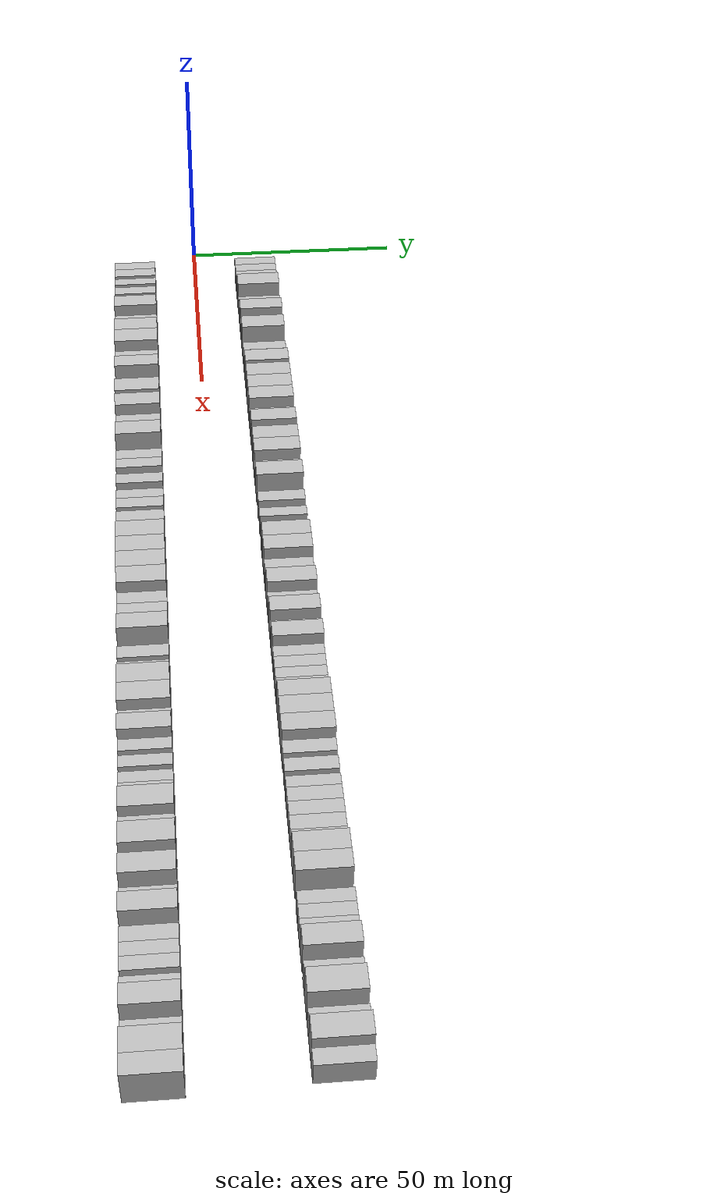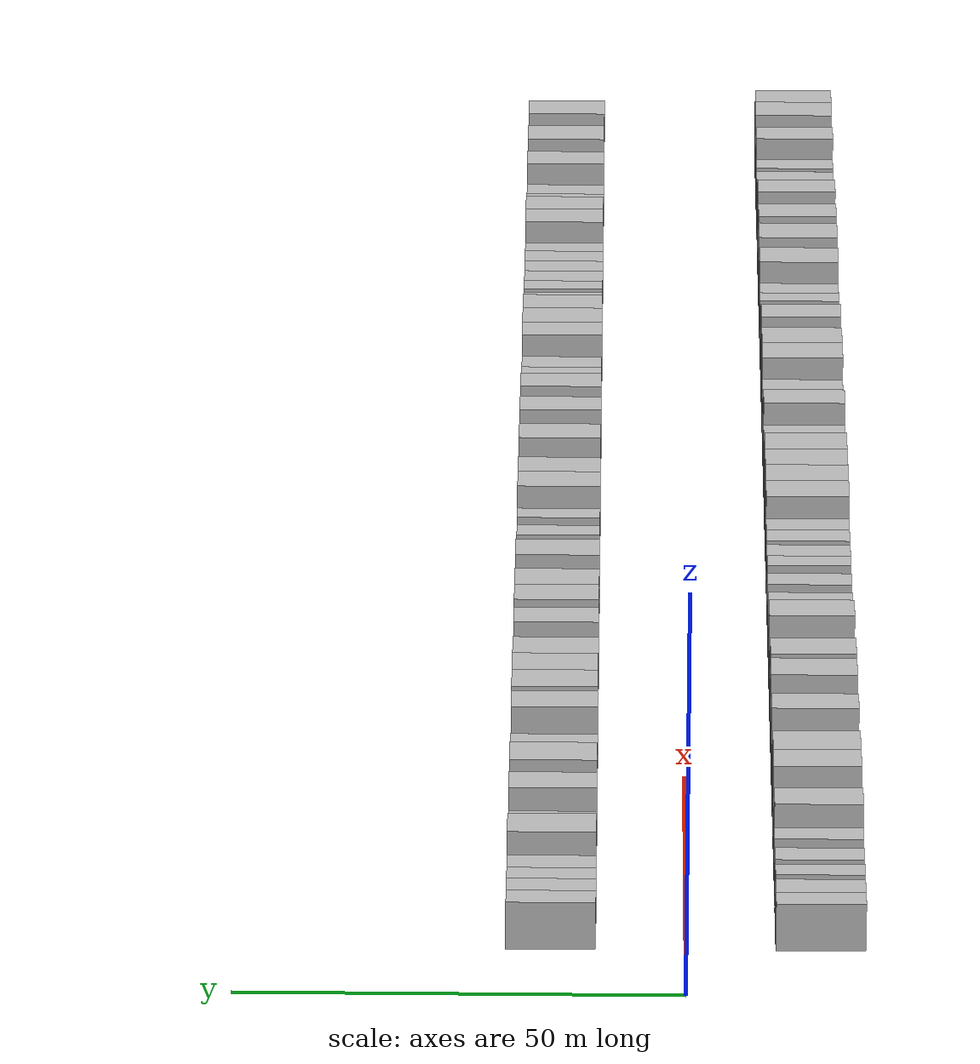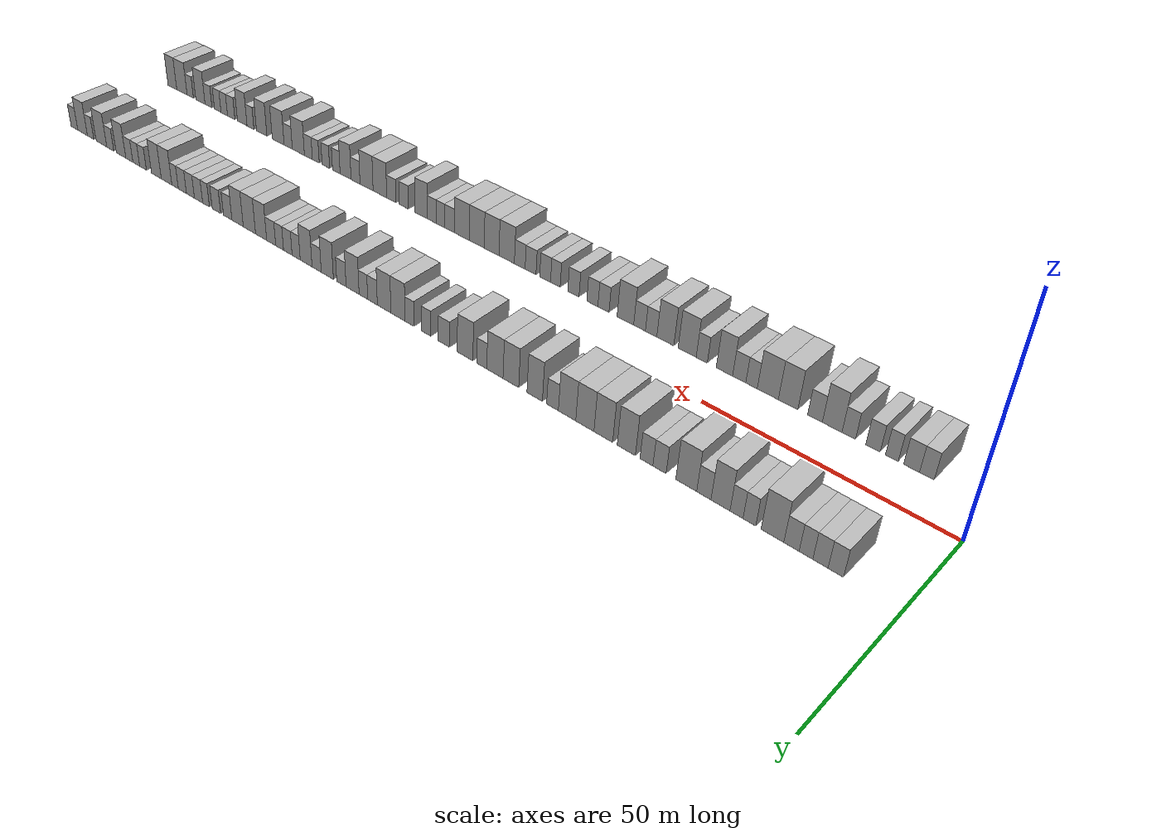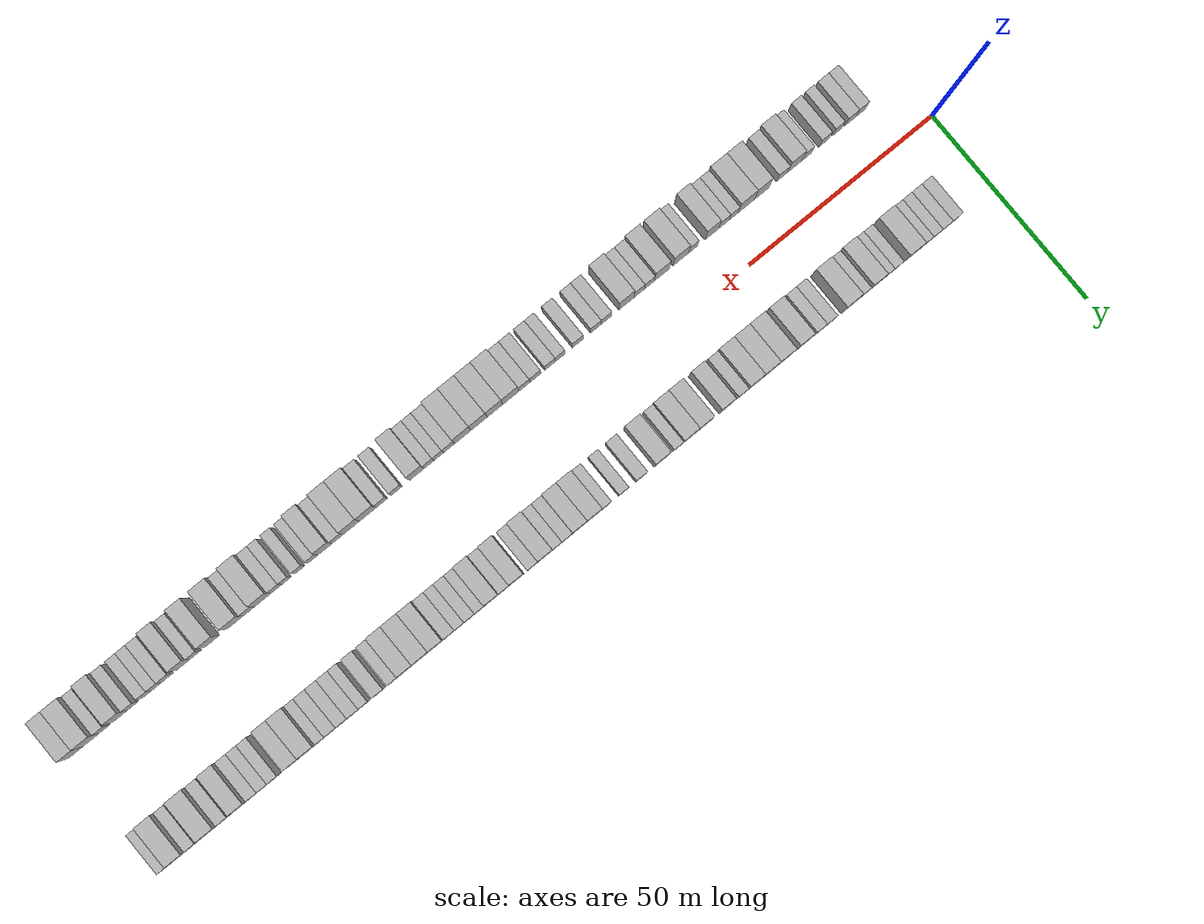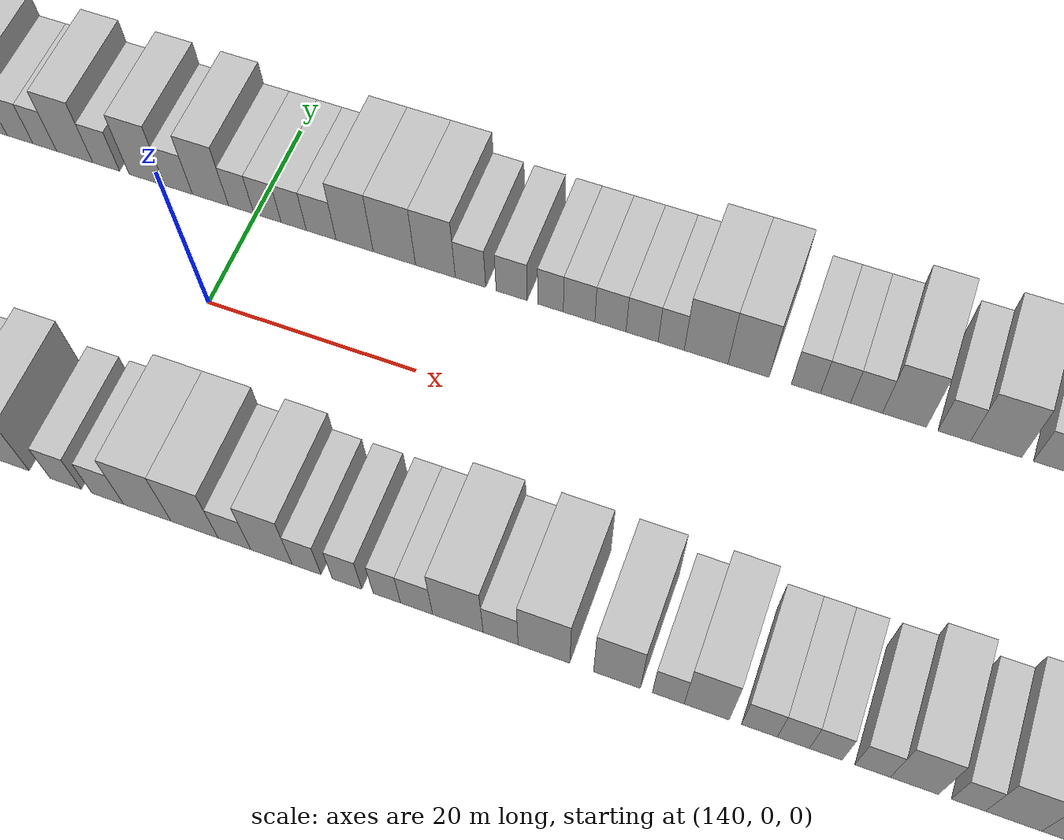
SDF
<sdf version="1.6">
 <world name="default">
  <scene>
   <sky><clouds><speed>12</speed></clouds></sky>
   <ambient>0.4 0.4 0.4 1</ambient>
   <background>0.7 0.7 0.7 1</background>
   <shadows>1</shadows>
  </scene>
  <gravity>0 0 -9.8066</gravity>
  <magnetic_field>6e-06 2.3e-05 -4.2e-05</magnetic_field>
  <physics default="0" name="default_physics" type="ode">
   <ode>
    <solver>
     <type>quick</type>
     <iters>10</iters>
     <sor>1.0</sor>
     <use_dynamic_moi_rescaling>0</use_dynamic_moi_rescaling>
    </solver>
    <constraints>
     <cfm>0</cfm>
     <erp>0.2</erp>
     <contact_max_correcting_vel>100</contact_max_correcting_vel>
     <contact_surface_layer>0.001</contact_surface_layer>
    </constraints>
   </ode>
   <max_step_size>0.004</max_step_size>
   <real_time_factor>1</real_time_factor>
   <real_time_update_rate>250</real_time_update_rate>
  </physics>
  <light name="sun" type="directional">
   <pose>0 0 10 0 0 0</pose>
   <diffuse>0.8 0.8 0.8 1</diffuse>
   <specular>0.2 0.2 0.2 1</specular>
   <attenuation>
    <range>1000</range>
    <constant>0.9</constant>
    <linear>0.01</linear>
    <quadratic>0.001</quadratic>
   </attenuation>
   <direction>-0.5 0.1 -0.9</direction>
  </light>
  <model name="building_1">
   <static>1</static>
   <pose>11.3598 15.0000 0 0.000000 0.000000 1.570796</pose>
   <link name="link">
    <pose>0 0 3.00 0 0 0</pose>
    <collision name="collision"><geometry><box><size>10.0000 2.7196 6.0000</size></box></geometry></collision>
    <visual name="visual">
     <cast_shadows>0</cast_shadows>
     <geometry><box><size>10.0000 2.7196 6.0000</size></box></geometry>
     <material>
      <script>
       <uri>model://HANNAS_wall/materials/scripts</uri>
       <uri>model://HANNAS_wall/materials/textures</uri>
       <name>vrc/HANNAS_wall</name>
      </script>
     </material>
    </visual>
   </link>
  </model>
  <model name="building_2">
   <static>1</static>
   <pose>14.0683 15.0000 0 0.000000 0.000000 1.570796</pose>
   <link name="link">
    <pose>0 0 3.00 0 0 0</pose>
    <collision name="collision"><geometry><box><size>10.0000 2.6974 6.0000</size></box></geometry></collision>
    <visual name="visual">
     <cast_shadows>0</cast_shadows>
     <geometry><box><size>10.0000 2.6974 6.0000</size></box></geometry>
     <material>
      <script>
       <uri>model://HANNAS_wall/materials/scripts</uri>
       <uri>model://HANNAS_wall/materials/textures</uri>
       <name>vrc/HANNAS_wall</name>
      </script>
     </material>
    </visual>
   </link>
  </model>
  <model name="building_3">
   <static>1</static>
   <pose>16.6501 15.0000 0 0.000000 0.000000 1.570796</pose>
   <link name="link">
    <pose>0 0 3.00 0 0 0</pose>
    <collision name="collision"><geometry><box><size>10.0000 2.4661 6.0000</size></box></geometry></collision>
    <visual name="visual">
     <cast_shadows>0</cast_shadows>
     <geometry><box><size>10.0000 2.4661 6.0000</size></box></geometry>
     <material>
      <script>
       <uri>model://HANNAS_wall/materials/scripts</uri>
       <uri>model://HANNAS_wall/materials/textures</uri>
       <name>vrc/HANNAS_wall</name>
      </script>
     </material>
    </visual>
   </link>
  </model>
  <model name="building_4">
   <static>1</static>
   <pose>19.2767 15.0000 0 0.000000 0.000000 1.570796</pose>
   <link name="link">
    <pose>0 0 3.00 0 0 0</pose>
    <collision name="collision"><geometry><box><size>10.0000 2.7872 6.0000</size></box></geometry></collision>
    <visual name="visual">
     <cast_shadows>0</cast_shadows>
     <geometry><box><size>10.0000 2.7872 6.0000</size></box></geometry>
     <material>
      <script>
       <uri>model://HANNAS_wall/materials/scripts</uri>
       <uri>model://HANNAS_wall/materials/textures</uri>
       <name>vrc/HANNAS_wall</name>
      </script>
     </material>
    </visual>
   </link>
  </model>
  <model name="building_5">
   <static>1</static>
   <pose>22.7889 15.0000 0 0.000000 0.000000 1.570796</pose>
   <link name="link">
    <pose>0 0 4.50 0 0 0</pose>
    <collision name="collision"><geometry><box><size>10.0000 4.2372 9.0000</size></box></geometry></collision>
    <visual name="visual">
     <cast_shadows>0</cast_shadows>
     <geometry><box><size>10.0000 4.2372 9.0000</size></box></geometry>
     <material>
      <script>
       <uri>model://HANNAS_wall/materials/scripts</uri>
       <uri>model://HANNAS_wall/materials/textures</uri>
       <name>vrc/HANNAS_wall</name>
      </script>
     </material>
    </visual>
   </link>
  </model>
  <model name="building_6">
   <static>1</static>
   <pose>27.1172 15.0000 0 0.000000 0.000000 1.570796</pose>
   <link name="link">
    <pose>0 0 3.00 0 0 0</pose>
    <collision name="collision"><geometry><box><size>10.0000 2.4193 6.0000</size></box></geometry></collision>
    <visual name="visual">
     <cast_shadows>0</cast_shadows>
     <geometry><box><size>10.0000 2.4193 6.0000</size></box></geometry>
     <material>
      <script>
       <uri>model://HANNAS_wall/materials/scripts</uri>
       <uri>model://HANNAS_wall/materials/textures</uri>
       <name>vrc/HANNAS_wall</name>
      </script>
     </material>
    </visual>
   </link>
  </model>
  <model name="building_7">
   <static>1</static>
   <pose>29.5809 15.0000 0 0.000000 0.000000 1.570796</pose>
   <link name="link">
    <pose>0 0 3.00 0 0 0</pose>
    <collision name="collision"><geometry><box><size>10.0000 2.5081 6.0000</size></box></geometry></collision>
    <visual name="visual">
     <cast_shadows>0</cast_shadows>
     <geometry><box><size>10.0000 2.5081 6.0000</size></box></geometry>
     <material>
      <script>
       <uri>model://HANNAS_wall/materials/scripts</uri>
       <uri>model://HANNAS_wall/materials/textures</uri>
       <name>vrc/HANNAS_wall</name>
      </script>
     </material>
    </visual>
   </link>
  </model>
  <model name="building_8">
   <static>1</static>
   <pose>32.6991 15.0000 0 0.000000 0.000000 1.570796</pose>
   <link name="link">
    <pose>0 0 4.50 0 0 0</pose>
    <collision name="collision"><geometry><box><size>10.0000 3.7283 9.0000</size></box></geometry></collision>
    <visual name="visual">
     <cast_shadows>0</cast_shadows>
     <geometry><box><size>10.0000 3.7283 9.0000</size></box></geometry>
     <material>
      <script>
       <uri>model://HANNAS_wall/materials/scripts</uri>
       <uri>model://HANNAS_wall/materials/textures</uri>
       <name>vrc/HANNAS_wall</name>
      </script>
     </material>
    </visual>
   </link>
  </model>
  <model name="building_9">
   <static>1</static>
   <pose>35.9825 15.0000 0 0.000000 0.000000 1.570796</pose>
   <link name="link">
    <pose>0 0 3.00 0 0 0</pose>
    <collision name="collision"><geometry><box><size>10.0000 2.8385 6.0000</size></box></geometry></collision>
    <visual name="visual">
     <cast_shadows>0</cast_shadows>
     <geometry><box><size>10.0000 2.8385 6.0000</size></box></geometry>
     <material>
      <script>
       <uri>model://HANNAS_wall/materials/scripts</uri>
       <uri>model://HANNAS_wall/materials/textures</uri>
       <name>vrc/HANNAS_wall</name>
      </script>
     </material>
    </visual>
   </link>
  </model>
  <model name="building_10">
   <static>1</static>
   <pose>39.5182 15.0000 0 0.000000 0.000000 1.570796</pose>
   <link name="link">
    <pose>0 0 4.50 0 0 0</pose>
    <collision name="collision"><geometry><box><size>10.0000 4.2330 9.0000</size></box></geometry></collision>
    <visual name="visual">
     <cast_shadows>0</cast_shadows>
     <geometry><box><size>10.0000 4.2330 9.0000</size></box></geometry>
     <material>
      <script>
       <uri>model://HANNAS_wall/materials/scripts</uri>
       <uri>model://HANNAS_wall/materials/textures</uri>
       <name>vrc/HANNAS_wall</name>
      </script>
     </material>
    </visual>
   </link>
  </model>
  <model name="building_11">
   <static>1</static>
   <pose>45.0125 15.0000 0 0.000000 0.000000 1.570796</pose>
   <link name="link">
    <pose>0 0 3.00 0 0 0</pose>
    <collision name="collision"><geometry><box><size>10.0000 2.7556 6.0000</size></box></geometry></collision>
    <visual name="visual">
     <cast_shadows>0</cast_shadows>
     <geometry><box><size>10.0000 2.7556 6.0000</size></box></geometry>
     <material>
      <script>
       <uri>model://HANNAS_wall/materials/scripts</uri>
       <uri>model://HANNAS_wall/materials/textures</uri>
       <name>vrc/HANNAS_wall</name>
      </script>
     </material>
    </visual>
   </link>
  </model>
  <model name="building_12">
   <static>1</static>
   <pose>47.7491 15.0000 0 0.000000 0.000000 1.570796</pose>
   <link name="link">
    <pose>0 0 3.00 0 0 0</pose>
    <collision name="collision"><geometry><box><size>10.0000 2.7178 6.0000</size></box></geometry></collision>
    <visual name="visual">
     <cast_shadows>0</cast_shadows>
     <geometry><box><size>10.0000 2.7178 6.0000</size></box></geometry>
     <material>
      <script>
       <uri>model://HANNAS_wall/materials/scripts</uri>
       <uri>model://HANNAS_wall/materials/textures</uri>
       <name>vrc/HANNAS_wall</name>
      </script>
     </material>
    </visual>
   </link>
  </model>
  <model name="building_13">
   <static>1</static>
   <pose>52.0646 15.0000 0 0.000000 0.000000 1.570796</pose>
   <link name="link">
    <pose>0 0 4.50 0 0 0</pose>
    <collision name="collision"><geometry><box><size>10.0000 3.9132 9.0000</size></box></geometry></collision>
    <visual name="visual">
     <cast_shadows>0</cast_shadows>
     <geometry><box><size>10.0000 3.9132 9.0000</size></box></geometry>
     <material>
      <script>
       <uri>model://HANNAS_wall/materials/scripts</uri>
       <uri>model://HANNAS_wall/materials/textures</uri>
       <name>vrc/HANNAS_wall</name>
      </script>
     </material>
    </visual>
   </link>
  </model>
  <model name="building_14">
   <static>1</static>
   <pose>57.0853 15.0000 0 0.000000 0.000000 1.570796</pose>
   <link name="link">
    <pose>0 0 4.50 0 0 0</pose>
    <collision name="collision"><geometry><box><size>10.0000 4.1283 9.0000</size></box></geometry></collision>
    <visual name="visual">
     <cast_shadows>0</cast_shadows>
     <geometry><box><size>10.0000 4.1283 9.0000</size></box></geometry>
     <material>
      <script>
       <uri>model://HANNAS_wall/materials/scripts</uri>
       <uri>model://HANNAS_wall/materials/textures</uri>
       <name>vrc/HANNAS_wall</name>
      </script>
     </material>
    </visual>
   </link>
  </model>
  <model name="building_15">
   <static>1</static>
   <pose>61.2078 15.0000 0 0.000000 0.000000 1.570796</pose>
   <link name="link">
    <pose>0 0 4.50 0 0 0</pose>
    <collision name="collision"><geometry><box><size>10.0000 4.1166 9.0000</size></box></geometry></collision>
    <visual name="visual">
     <cast_shadows>0</cast_shadows>
     <geometry><box><size>10.0000 4.1166 9.0000</size></box></geometry>
     <material>
      <script>
       <uri>model://HANNAS_wall/materials/scripts</uri>
       <uri>model://HANNAS_wall/materials/textures</uri>
       <name>vrc/HANNAS_wall</name>
      </script>
     </material>
    </visual>
   </link>
  </model>
  <model name="building_16">
   <static>1</static>
   <pose>65.2668 15.0000 0 0.000000 0.000000 1.570796</pose>
   <link name="link">
    <pose>0 0 4.50 0 0 0</pose>
    <collision name="collision"><geometry><box><size>10.0000 4.0015 9.0000</size></box></geometry></collision>
    <visual name="visual">
     <cast_shadows>0</cast_shadows>
     <geometry><box><size>10.0000 4.0015 9.0000</size></box></geometry>
     <material>
      <script>
       <uri>model://HANNAS_wall/materials/scripts</uri>
       <uri>model://HANNAS_wall/materials/textures</uri>
       <name>vrc/HANNAS_wall</name>
      </script>
     </material>
    </visual>
   </link>
  </model>
  <model name="building_17">
   <static>1</static>
   <pose>68.6369 15.0000 0 0.000000 0.000000 1.570796</pose>
   <link name="link">
    <pose>0 0 3.00 0 0 0</pose>
    <collision name="collision"><geometry><box><size>10.0000 2.7386 6.0000</size></box></geometry></collision>
    <visual name="visual">
     <cast_shadows>0</cast_shadows>
     <geometry><box><size>10.0000 2.7386 6.0000</size></box></geometry>
     <material>
      <script>
       <uri>model://HANNAS_wall/materials/scripts</uri>
       <uri>model://HANNAS_wall/materials/textures</uri>
       <name>vrc/HANNAS_wall</name>
      </script>
     </material>
    </visual>
   </link>
  </model>
  <model name="building_18">
   <static>1</static>
   <pose>72.8464 15.0000 0 0.000000 0.000000 1.570796</pose>
   <link name="link">
    <pose>0 0 4.50 0 0 0</pose>
    <collision name="collision"><geometry><box><size>10.0000 3.6804 9.0000</size></box></geometry></collision>
    <visual name="visual">
     <cast_shadows>0</cast_shadows>
     <geometry><box><size>10.0000 3.6804 9.0000</size></box></geometry>
     <material>
      <script>
       <uri>model://HANNAS_wall/materials/scripts</uri>
       <uri>model://HANNAS_wall/materials/textures</uri>
       <name>vrc/HANNAS_wall</name>
      </script>
     </material>
    </visual>
   </link>
  </model>
  <model name="building_19">
   <static>1</static>
   <pose>78.6091 15.0000 0 0.000000 0.000000 1.570796</pose>
   <link name="link">
    <pose>0 0 4.50 0 0 0</pose>
    <collision name="collision"><geometry><box><size>10.0000 3.8452 9.0000</size></box></geometry></collision>
    <visual name="visual">
     <cast_shadows>0</cast_shadows>
     <geometry><box><size>10.0000 3.8452 9.0000</size></box></geometry>
     <material>
      <script>
       <uri>model://HANNAS_wall/materials/scripts</uri>
       <uri>model://HANNAS_wall/materials/textures</uri>
       <name>vrc/HANNAS_wall</name>
      </script>
     </material>
    </visual>
   </link>
  </model>
  <model name="building_20">
   <static>1</static>
   <pose>82.5596 15.0000 0 0.000000 0.000000 1.570796</pose>
   <link name="link">
    <pose>0 0 4.50 0 0 0</pose>
    <collision name="collision"><geometry><box><size>10.0000 4.0557 9.0000</size></box></geometry></collision>
    <visual name="visual">
     <cast_shadows>0</cast_shadows>
     <geometry><box><size>10.0000 4.0557 9.0000</size></box></geometry>
     <material>
      <script>
       <uri>model://HANNAS_wall/materials/scripts</uri>
       <uri>model://HANNAS_wall/materials/textures</uri>
       <name>vrc/HANNAS_wall</name>
      </script>
     </material>
    </visual>
   </link>
  </model>
  <model name="building_21">
   <static>1</static>
   <pose>85.8498 15.0000 0 0.000000 0.000000 1.570796</pose>
   <link name="link">
    <pose>0 0 3.00 0 0 0</pose>
    <collision name="collision"><geometry><box><size>10.0000 2.5248 6.0000</size></box></geometry></collision>
    <visual name="visual">
     <cast_shadows>0</cast_shadows>
     <geometry><box><size>10.0000 2.5248 6.0000</size></box></geometry>
     <material>
      <script>
       <uri>model://HANNAS_wall/materials/scripts</uri>
       <uri>model://HANNAS_wall/materials/textures</uri>
       <name>vrc/HANNAS_wall</name>
      </script>
     </material>
    </visual>
   </link>
  </model>
  <model name="building_22">
   <static>1</static>
   <pose>90.1329 15.0000 0 0.000000 0.000000 1.570796</pose>
   <link name="link">
    <pose>0 0 4.50 0 0 0</pose>
    <collision name="collision"><geometry><box><size>10.0000 4.0415 9.0000</size></box></geometry></collision>
    <visual name="visual">
     <cast_shadows>0</cast_shadows>
     <geometry><box><size>10.0000 4.0415 9.0000</size></box></geometry>
     <material>
      <script>
       <uri>model://HANNAS_wall/materials/scripts</uri>
       <uri>model://HANNAS_wall/materials/textures</uri>
       <name>vrc/HANNAS_wall</name>
      </script>
     </material>
    </visual>
   </link>
  </model>
  <model name="building_23">
   <static>1</static>
   <pose>95.6422 15.0000 0 0.000000 0.000000 1.570796</pose>
   <link name="link">
    <pose>0 0 3.00 0 0 0</pose>
    <collision name="collision"><geometry><box><size>10.0000 2.9771 6.0000</size></box></geometry></collision>
    <visual name="visual">
     <cast_shadows>0</cast_shadows>
     <geometry><box><size>10.0000 2.9771 6.0000</size></box></geometry>
     <material>
      <script>
       <uri>model://HANNAS_wall/materials/scripts</uri>
       <uri>model://HANNAS_wall/materials/textures</uri>
       <name>vrc/HANNAS_wall</name>
      </script>
     </material>
    </visual>
   </link>
  </model>
  <model name="building_24">
   <static>1</static>
   <pose>100.4237 15.0000 0 0.000000 0.000000 1.570796</pose>
   <link name="link">
    <pose>0 0 3.00 0 0 0</pose>
    <collision name="collision"><geometry><box><size>10.0000 2.5860 6.0000</size></box></geometry></collision>
    <visual name="visual">
     <cast_shadows>0</cast_shadows>
     <geometry><box><size>10.0000 2.5860 6.0000</size></box></geometry>
     <material>
      <script>
       <uri>model://HANNAS_wall/materials/scripts</uri>
       <uri>model://HANNAS_wall/materials/textures</uri>
       <name>vrc/HANNAS_wall</name>
      </script>
     </material>
    </visual>
   </link>
  </model>
  <model name="building_25">
   <static>1</static>
   <pose>104.9449 15.0000 0 0.000000 0.000000 1.570796</pose>
   <link name="link">
    <pose>0 0 3.00 0 0 0</pose>
    <collision name="collision"><geometry><box><size>10.0000 2.4564 6.0000</size></box></geometry></collision>
    <visual name="visual">
     <cast_shadows>0</cast_shadows>
     <geometry><box><size>10.0000 2.4564 6.0000</size></box></geometry>
     <material>
      <script>
       <uri>model://HANNAS_wall/materials/scripts</uri>
       <uri>model://HANNAS_wall/materials/textures</uri>
       <name>vrc/HANNAS_wall</name>
      </script>
     </material>
    </visual>
   </link>
  </model>
  <model name="building_26">
   <static>1</static>
   <pose>108.1541 15.0000 0 0.000000 0.000000 1.570796</pose>
   <link name="link">
    <pose>0 0 4.50 0 0 0</pose>
    <collision name="collision"><geometry><box><size>10.0000 3.9619 9.0000</size></box></geometry></collision>
    <visual name="visual">
     <cast_shadows>0</cast_shadows>
     <geometry><box><size>10.0000 3.9619 9.0000</size></box></geometry>
     <material>
      <script>
       <uri>model://HANNAS_wall/materials/scripts</uri>
       <uri>model://HANNAS_wall/materials/textures</uri>
       <name>vrc/HANNAS_wall</name>
      </script>
     </material>
    </visual>
   </link>
  </model>
  <model name="building_27">
   <static>1</static>
   <pose>112.0646 15.0000 0 0.000000 0.000000 1.570796</pose>
   <link name="link">
    <pose>0 0 4.50 0 0 0</pose>
    <collision name="collision"><geometry><box><size>10.0000 3.8592 9.0000</size></box></geometry></collision>
    <visual name="visual">
     <cast_shadows>0</cast_shadows>
     <geometry><box><size>10.0000 3.8592 9.0000</size></box></geometry>
     <material>
      <script>
       <uri>model://HANNAS_wall/materials/scripts</uri>
       <uri>model://HANNAS_wall/materials/textures</uri>
       <name>vrc/HANNAS_wall</name>
      </script>
     </material>
    </visual>
   </link>
  </model>
  <model name="building_28">
   <static>1</static>
   <pose>115.3843 15.0000 0 0.000000 0.000000 1.570796</pose>
   <link name="link">
    <pose>0 0 3.00 0 0 0</pose>
    <collision name="collision"><geometry><box><size>10.0000 2.7801 6.0000</size></box></geometry></collision>
    <visual name="visual">
     <cast_shadows>0</cast_shadows>
     <geometry><box><size>10.0000 2.7801 6.0000</size></box></geometry>
     <material>
      <script>
       <uri>model://HANNAS_wall/materials/scripts</uri>
       <uri>model://HANNAS_wall/materials/textures</uri>
       <name>vrc/HANNAS_wall</name>
      </script>
     </material>
    </visual>
   </link>
  </model>
  <model name="building_29">
   <static>1</static>
   <pose>118.0255 15.0000 0 0.000000 0.000000 1.570796</pose>
   <link name="link">
    <pose>0 0 3.00 0 0 0</pose>
    <collision name="collision"><geometry><box><size>10.0000 2.5024 6.0000</size></box></geometry></collision>
    <visual name="visual">
     <cast_shadows>0</cast_shadows>
     <geometry><box><size>10.0000 2.5024 6.0000</size></box></geometry>
     <material>
      <script>
       <uri>model://HANNAS_wall/materials/scripts</uri>
       <uri>model://HANNAS_wall/materials/textures</uri>
       <name>vrc/HANNAS_wall</name>
      </script>
     </material>
    </visual>
   </link>
  </model>
  <model name="building_30">
   <static>1</static>
   <pose>121.2008 15.0000 0 0.000000 0.000000 1.570796</pose>
   <link name="link">
    <pose>0 0 4.50 0 0 0</pose>
    <collision name="collision"><geometry><box><size>10.0000 3.8482 9.0000</size></box></geometry></collision>
    <visual name="visual">
     <cast_shadows>0</cast_shadows>
     <geometry><box><size>10.0000 3.8482 9.0000</size></box></geometry>
     <material>
      <script>
       <uri>model://HANNAS_wall/materials/scripts</uri>
       <uri>model://HANNAS_wall/materials/textures</uri>
       <name>vrc/HANNAS_wall</name>
      </script>
     </material>
    </visual>
   </link>
  </model>
  <model name="building_31">
   <static>1</static>
   <pose>124.5239 15.0000 0 0.000000 0.000000 1.570796</pose>
   <link name="link">
    <pose>0 0 3.00 0 0 0</pose>
    <collision name="collision"><geometry><box><size>10.0000 2.7982 6.0000</size></box></geometry></collision>
    <visual name="visual">
     <cast_shadows>0</cast_shadows>
     <geometry><box><size>10.0000 2.7982 6.0000</size></box></geometry>
     <material>
      <script>
       <uri>model://HANNAS_wall/materials/scripts</uri>
       <uri>model://HANNAS_wall/materials/textures</uri>
       <name>vrc/HANNAS_wall</name>
      </script>
     </material>
    </visual>
   </link>
  </model>
  <model name="building_32">
   <static>1</static>
   <pose>128.7800 15.0000 0 0.000000 0.000000 1.570796</pose>
   <link name="link">
    <pose>0 0 4.50 0 0 0</pose>
    <collision name="collision"><geometry><box><size>10.0000 3.7140 9.0000</size></box></geometry></collision>
    <visual name="visual">
     <cast_shadows>0</cast_shadows>
     <geometry><box><size>10.0000 3.7140 9.0000</size></box></geometry>
     <material>
      <script>
       <uri>model://HANNAS_wall/materials/scripts</uri>
       <uri>model://HANNAS_wall/materials/textures</uri>
       <name>vrc/HANNAS_wall</name>
      </script>
     </material>
    </visual>
   </link>
  </model>
  <model name="building_33">
   <static>1</static>
   <pose>132.0614 15.0000 0 0.000000 0.000000 1.570796</pose>
   <link name="link">
    <pose>0 0 3.00 0 0 0</pose>
    <collision name="collision"><geometry><box><size>10.0000 2.8488 6.0000</size></box></geometry></collision>
    <visual name="visual">
     <cast_shadows>0</cast_shadows>
     <geometry><box><size>10.0000 2.8488 6.0000</size></box></geometry>
     <material>
      <script>
       <uri>model://HANNAS_wall/materials/scripts</uri>
       <uri>model://HANNAS_wall/materials/textures</uri>
       <name>vrc/HANNAS_wall</name>
      </script>
     </material>
    </visual>
   </link>
  </model>
  <model name="building_34">
   <static>1</static>
   <pose>135.3368 15.0000 0 0.000000 0.000000 1.570796</pose>
   <link name="link">
    <pose>0 0 4.50 0 0 0</pose>
    <collision name="collision"><geometry><box><size>10.0000 3.7020 9.0000</size></box></geometry></collision>
    <visual name="visual">
     <cast_shadows>0</cast_shadows>
     <geometry><box><size>10.0000 3.7020 9.0000</size></box></geometry>
     <material>
      <script>
       <uri>model://HANNAS_wall/materials/scripts</uri>
       <uri>model://HANNAS_wall/materials/textures</uri>
       <name>vrc/HANNAS_wall</name>
      </script>
     </material>
    </visual>
   </link>
  </model>
  <model name="building_35">
   <static>1</static>
   <pose>138.4774 15.0000 0 0.000000 0.000000 1.570796</pose>
   <link name="link">
    <pose>0 0 3.00 0 0 0</pose>
    <collision name="collision"><geometry><box><size>10.0000 2.5791 6.0000</size></box></geometry></collision>
    <visual name="visual">
     <cast_shadows>0</cast_shadows>
     <geometry><box><size>10.0000 2.5791 6.0000</size></box></geometry>
     <material>
      <script>
       <uri>model://HANNAS_wall/materials/scripts</uri>
       <uri>model://HANNAS_wall/materials/textures</uri>
       <name>vrc/HANNAS_wall</name>
      </script>
     </material>
    </visual>
   </link>
  </model>
  <model name="building_36">
   <static>1</static>
   <pose>141.1463 15.0000 0 0.000000 0.000000 1.570796</pose>
   <link name="link">
    <pose>0 0 3.00 0 0 0</pose>
    <collision name="collision"><geometry><box><size>10.0000 2.7586 6.0000</size></box></geometry></collision>
    <visual name="visual">
     <cast_shadows>0</cast_shadows>
     <geometry><box><size>10.0000 2.7586 6.0000</size></box></geometry>
     <material>
      <script>
       <uri>model://HANNAS_wall/materials/scripts</uri>
       <uri>model://HANNAS_wall/materials/textures</uri>
       <name>vrc/HANNAS_wall</name>
      </script>
     </material>
    </visual>
   </link>
  </model>
  <model name="building_37">
   <static>1</static>
   <pose>143.7925 15.0000 0 0.000000 0.000000 1.570796</pose>
   <link name="link">
    <pose>0 0 3.00 0 0 0</pose>
    <collision name="collision"><geometry><box><size>10.0000 2.5339 6.0000</size></box></geometry></collision>
    <visual name="visual">
     <cast_shadows>0</cast_shadows>
     <geometry><box><size>10.0000 2.5339 6.0000</size></box></geometry>
     <material>
      <script>
       <uri>model://HANNAS_wall/materials/scripts</uri>
       <uri>model://HANNAS_wall/materials/textures</uri>
       <name>vrc/HANNAS_wall</name>
      </script>
     </material>
    </visual>
   </link>
  </model>
  <model name="building_38">
   <static>1</static>
   <pose>146.5416 15.0000 0 0.000000 0.000000 1.570796</pose>
   <link name="link">
    <pose>0 0 3.00 0 0 0</pose>
    <collision name="collision"><geometry><box><size>10.0000 2.9643 6.0000</size></box></geometry></collision>
    <visual name="visual">
     <cast_shadows>0</cast_shadows>
     <geometry><box><size>10.0000 2.9643 6.0000</size></box></geometry>
     <material>
      <script>
       <uri>model://HANNAS_wall/materials/scripts</uri>
       <uri>model://HANNAS_wall/materials/textures</uri>
       <name>vrc/HANNAS_wall</name>
      </script>
     </material>
    </visual>
   </link>
  </model>
  <model name="building_39">
   <static>1</static>
   <pose>149.8689 15.0000 0 0.000000 0.000000 1.570796</pose>
   <link name="link">
    <pose>0 0 4.50 0 0 0</pose>
    <collision name="collision"><geometry><box><size>10.0000 3.6902 9.0000</size></box></geometry></collision>
    <visual name="visual">
     <cast_shadows>0</cast_shadows>
     <geometry><box><size>10.0000 3.6902 9.0000</size></box></geometry>
     <material>
      <script>
       <uri>model://HANNAS_wall/materials/scripts</uri>
       <uri>model://HANNAS_wall/materials/textures</uri>
       <name>vrc/HANNAS_wall</name>
      </script>
     </material>
    </visual>
   </link>
  </model>
  <model name="building_40">
   <static>1</static>
   <pose>153.7895 15.0000 0 0.000000 0.000000 1.570796</pose>
   <link name="link">
    <pose>0 0 4.50 0 0 0</pose>
    <collision name="collision"><geometry><box><size>10.0000 4.1510 9.0000</size></box></geometry></collision>
    <visual name="visual">
     <cast_shadows>0</cast_shadows>
     <geometry><box><size>10.0000 4.1510 9.0000</size></box></geometry>
     <material>
      <script>
       <uri>model://HANNAS_wall/materials/scripts</uri>
       <uri>model://HANNAS_wall/materials/textures</uri>
       <name>vrc/HANNAS_wall</name>
      </script>
     </material>
    </visual>
   </link>
  </model>
  <model name="building_41">
   <static>1</static>
   <pose>157.8020 15.0000 0 0.000000 0.000000 1.570796</pose>
   <link name="link">
    <pose>0 0 4.50 0 0 0</pose>
    <collision name="collision"><geometry><box><size>10.0000 3.8740 9.0000</size></box></geometry></collision>
    <visual name="visual">
     <cast_shadows>0</cast_shadows>
     <geometry><box><size>10.0000 3.8740 9.0000</size></box></geometry>
     <material>
      <script>
       <uri>model://HANNAS_wall/materials/scripts</uri>
       <uri>model://HANNAS_wall/materials/textures</uri>
       <name>vrc/HANNAS_wall</name>
      </script>
     </material>
    </visual>
   </link>
  </model>
  <model name="building_42">
   <static>1</static>
   <pose>161.2096 15.0000 0 0.000000 0.000000 1.570796</pose>
   <link name="link">
    <pose>0 0 3.00 0 0 0</pose>
    <collision name="collision"><geometry><box><size>10.0000 2.9412 6.0000</size></box></geometry></collision>
    <visual name="visual">
     <cast_shadows>0</cast_shadows>
     <geometry><box><size>10.0000 2.9412 6.0000</size></box></geometry>
     <material>
      <script>
       <uri>model://HANNAS_wall/materials/scripts</uri>
       <uri>model://HANNAS_wall/materials/textures</uri>
       <name>vrc/HANNAS_wall</name>
      </script>
     </material>
    </visual>
   </link>
  </model>
  <model name="building_43">
   <static>1</static>
   <pose>165.1654 15.0000 0 0.000000 0.000000 1.570796</pose>
   <link name="link">
    <pose>0 0 3.00 0 0 0</pose>
    <collision name="collision"><geometry><box><size>10.0000 2.9705 6.0000</size></box></geometry></collision>
    <visual name="visual">
     <cast_shadows>0</cast_shadows>
     <geometry><box><size>10.0000 2.9705 6.0000</size></box></geometry>
     <material>
      <script>
       <uri>model://HANNAS_wall/materials/scripts</uri>
       <uri>model://HANNAS_wall/materials/textures</uri>
       <name>vrc/HANNAS_wall</name>
      </script>
     </material>
    </visual>
   </link>
  </model>
  <model name="building_44">
   <static>1</static>
   <pose>168.8635 15.0000 0 0.000000 0.000000 1.570796</pose>
   <link name="link">
    <pose>0 0 3.00 0 0 0</pose>
    <collision name="collision"><geometry><box><size>10.0000 2.4256 6.0000</size></box></geometry></collision>
    <visual name="visual">
     <cast_shadows>0</cast_shadows>
     <geometry><box><size>10.0000 2.4256 6.0000</size></box></geometry>
     <material>
      <script>
       <uri>model://HANNAS_wall/materials/scripts</uri>
       <uri>model://HANNAS_wall/materials/textures</uri>
       <name>vrc/HANNAS_wall</name>
      </script>
     </material>
    </visual>
   </link>
  </model>
  <model name="building_45">
   <static>1</static>
   <pose>171.5646 15.0000 0 0.000000 0.000000 1.570796</pose>
   <link name="link">
    <pose>0 0 3.00 0 0 0</pose>
    <collision name="collision"><geometry><box><size>10.0000 2.9766 6.0000</size></box></geometry></collision>
    <visual name="visual">
     <cast_shadows>0</cast_shadows>
     <geometry><box><size>10.0000 2.9766 6.0000</size></box></geometry>
     <material>
      <script>
       <uri>model://HANNAS_wall/materials/scripts</uri>
       <uri>model://HANNAS_wall/materials/textures</uri>
       <name>vrc/HANNAS_wall</name>
      </script>
     </material>
    </visual>
   </link>
  </model>
  <model name="building_46">
   <static>1</static>
   <pose>174.5100 15.0000 0 0.000000 0.000000 1.570796</pose>
   <link name="link">
    <pose>0 0 3.00 0 0 0</pose>
    <collision name="collision"><geometry><box><size>10.0000 2.9141 6.0000</size></box></geometry></collision>
    <visual name="visual">
     <cast_shadows>0</cast_shadows>
     <geometry><box><size>10.0000 2.9141 6.0000</size></box></geometry>
     <material>
      <script>
       <uri>model://HANNAS_wall/materials/scripts</uri>
       <uri>model://HANNAS_wall/materials/textures</uri>
       <name>vrc/HANNAS_wall</name>
      </script>
     </material>
    </visual>
   </link>
  </model>
  <model name="building_47">
   <static>1</static>
   <pose>177.4632 15.0000 0 0.000000 0.000000 1.570796</pose>
   <link name="link">
    <pose>0 0 3.00 0 0 0</pose>
    <collision name="collision"><geometry><box><size>10.0000 2.9924 6.0000</size></box></geometry></collision>
    <visual name="visual">
     <cast_shadows>0</cast_shadows>
     <geometry><box><size>10.0000 2.9924 6.0000</size></box></geometry>
     <material>
      <script>
       <uri>model://HANNAS_wall/materials/scripts</uri>
       <uri>model://HANNAS_wall/materials/textures</uri>
       <name>vrc/HANNAS_wall</name>
      </script>
     </material>
    </visual>
   </link>
  </model>
  <model name="building_48">
   <static>1</static>
   <pose>180.1617 15.0000 0 0.000000 0.000000 1.570796</pose>
   <link name="link">
    <pose>0 0 3.00 0 0 0</pose>
    <collision name="collision"><geometry><box><size>10.0000 2.4045 6.0000</size></box></geometry></collision>
    <visual name="visual">
     <cast_shadows>0</cast_shadows>
     <geometry><box><size>10.0000 2.4045 6.0000</size></box></geometry>
     <material>
      <script>
       <uri>model://HANNAS_wall/materials/scripts</uri>
       <uri>model://HANNAS_wall/materials/textures</uri>
       <name>vrc/HANNAS_wall</name>
      </script>
     </material>
    </visual>
   </link>
  </model>
  <model name="building_49">
   <static>1</static>
   <pose>183.3713 15.0000 0 0.000000 0.000000 1.570796</pose>
   <link name="link">
    <pose>0 0 4.50 0 0 0</pose>
    <collision name="collision"><geometry><box><size>10.0000 4.0148 9.0000</size></box></geometry></collision>
    <visual name="visual">
     <cast_shadows>0</cast_shadows>
     <geometry><box><size>10.0000 4.0148 9.0000</size></box></geometry>
     <material>
      <script>
       <uri>model://HANNAS_wall/materials/scripts</uri>
       <uri>model://HANNAS_wall/materials/textures</uri>
       <name>vrc/HANNAS_wall</name>
      </script>
     </material>
    </visual>
   </link>
  </model>
  <model name="building_50">
   <static>1</static>
   <pose>187.2475 15.0000 0 0.000000 0.000000 1.570796</pose>
   <link name="link">
    <pose>0 0 4.50 0 0 0</pose>
    <collision name="collision"><geometry><box><size>10.0000 3.7375 9.0000</size></box></geometry></collision>
    <visual name="visual">
     <cast_shadows>0</cast_shadows>
     <geometry><box><size>10.0000 3.7375 9.0000</size></box></geometry>
     <material>
      <script>
       <uri>model://HANNAS_wall/materials/scripts</uri>
       <uri>model://HANNAS_wall/materials/textures</uri>
       <name>vrc/HANNAS_wall</name>
      </script>
     </material>
    </visual>
   </link>
  </model>
  <model name="building_51">
   <static>1</static>
   <pose>192.4228 15.0000 0 0.000000 0.000000 1.570796</pose>
   <link name="link">
    <pose>0 0 3.00 0 0 0</pose>
    <collision name="collision"><geometry><box><size>10.0000 2.6130 6.0000</size></box></geometry></collision>
    <visual name="visual">
     <cast_shadows>0</cast_shadows>
     <geometry><box><size>10.0000 2.6130 6.0000</size></box></geometry>
     <material>
      <script>
       <uri>model://HANNAS_wall/materials/scripts</uri>
       <uri>model://HANNAS_wall/materials/textures</uri>
       <name>vrc/HANNAS_wall</name>
      </script>
     </material>
    </visual>
   </link>
  </model>
  <model name="building_52">
   <static>1</static>
   <pose>195.0679 15.0000 0 0.000000 0.000000 1.570796</pose>
   <link name="link">
    <pose>0 0 3.00 0 0 0</pose>
    <collision name="collision"><geometry><box><size>10.0000 2.6773 6.0000</size></box></geometry></collision>
    <visual name="visual">
     <cast_shadows>0</cast_shadows>
     <geometry><box><size>10.0000 2.6773 6.0000</size></box></geometry>
     <material>
      <script>
       <uri>model://HANNAS_wall/materials/scripts</uri>
       <uri>model://HANNAS_wall/materials/textures</uri>
       <name>vrc/HANNAS_wall</name>
      </script>
     </material>
    </visual>
   </link>
  </model>
  <model name="building_53">
   <static>1</static>
   <pose>197.8263 15.0000 0 0.000000 0.000000 1.570796</pose>
   <link name="link">
    <pose>0 0 3.00 0 0 0</pose>
    <collision name="collision"><geometry><box><size>10.0000 2.8395 6.0000</size></box></geometry></collision>
    <visual name="visual">
     <cast_shadows>0</cast_shadows>
     <geometry><box><size>10.0000 2.8395 6.0000</size></box></geometry>
     <material>
      <script>
       <uri>model://HANNAS_wall/materials/scripts</uri>
       <uri>model://HANNAS_wall/materials/textures</uri>
       <name>vrc/HANNAS_wall</name>
      </script>
     </material>
    </visual>
   </link>
  </model>
  <model name="building_54">
   <static>1</static>
   <pose>201.1836 15.0000 0 0.000000 0.000000 1.570796</pose>
   <link name="link">
    <pose>0 0 4.50 0 0 0</pose>
    <collision name="collision"><geometry><box><size>10.0000 3.8752 9.0000</size></box></geometry></collision>
    <visual name="visual">
     <cast_shadows>0</cast_shadows>
     <geometry><box><size>10.0000 3.8752 9.0000</size></box></geometry>
     <material>
      <script>
       <uri>model://HANNAS_wall/materials/scripts</uri>
       <uri>model://HANNAS_wall/materials/textures</uri>
       <name>vrc/HANNAS_wall</name>
      </script>
     </material>
    </visual>
   </link>
  </model>
  <model name="building_55">
   <static>1</static>
   <pose>205.5317 15.0000 0 0.000000 0.000000 1.570796</pose>
   <link name="link">
    <pose>0 0 3.00 0 0 0</pose>
    <collision name="collision"><geometry><box><size>10.0000 2.8210 6.0000</size></box></geometry></collision>
    <visual name="visual">
     <cast_shadows>0</cast_shadows>
     <geometry><box><size>10.0000 2.8210 6.0000</size></box></geometry>
     <material>
      <script>
       <uri>model://HANNAS_wall/materials/scripts</uri>
       <uri>model://HANNAS_wall/materials/textures</uri>
       <name>vrc/HANNAS_wall</name>
      </script>
     </material>
    </visual>
   </link>
  </model>
  <model name="building_56">
   <static>1</static>
   <pose>209.1608 15.0000 0 0.000000 0.000000 1.570796</pose>
   <link name="link">
    <pose>0 0 4.50 0 0 0</pose>
    <collision name="collision"><geometry><box><size>10.0000 4.4372 9.0000</size></box></geometry></collision>
    <visual name="visual">
     <cast_shadows>0</cast_shadows>
     <geometry><box><size>10.0000 4.4372 9.0000</size></box></geometry>
     <material>
      <script>
       <uri>model://HANNAS_wall/materials/scripts</uri>
       <uri>model://HANNAS_wall/materials/textures</uri>
       <name>vrc/HANNAS_wall</name>
      </script>
     </material>
    </visual>
   </link>
  </model>
  <model name="building_57">
   <static>1</static>
   <pose>213.7169 15.0000 0 0.000000 0.000000 1.570796</pose>
   <link name="link">
    <pose>0 0 3.00 0 0 0</pose>
    <collision name="collision"><geometry><box><size>10.0000 2.6751 6.0000</size></box></geometry></collision>
    <visual name="visual">
     <cast_shadows>0</cast_shadows>
     <geometry><box><size>10.0000 2.6751 6.0000</size></box></geometry>
     <material>
      <script>
       <uri>model://HANNAS_wall/materials/scripts</uri>
       <uri>model://HANNAS_wall/materials/textures</uri>
       <name>vrc/HANNAS_wall</name>
      </script>
     </material>
    </visual>
   </link>
  </model>
  <model name="building_58">
   <static>1</static>
   <pose>217.1153 15.0000 0 0.000000 0.000000 1.570796</pose>
   <link name="link">
    <pose>0 0 4.50 0 0 0</pose>
    <collision name="collision"><geometry><box><size>10.0000 4.1216 9.0000</size></box></geometry></collision>
    <visual name="visual">
     <cast_shadows>0</cast_shadows>
     <geometry><box><size>10.0000 4.1216 9.0000</size></box></geometry>
     <material>
      <script>
       <uri>model://HANNAS_wall/materials/scripts</uri>
       <uri>model://HANNAS_wall/materials/textures</uri>
       <name>vrc/HANNAS_wall</name>
      </script>
     </material>
    </visual>
   </link>
  </model>
  <model name="building_59">
   <static>1</static>
   <pose>220.6098 15.0000 0 0.000000 0.000000 1.570796</pose>
   <link name="link">
    <pose>0 0 3.00 0 0 0</pose>
    <collision name="collision"><geometry><box><size>10.0000 2.8673 6.0000</size></box></geometry></collision>
    <visual name="visual">
     <cast_shadows>0</cast_shadows>
     <geometry><box><size>10.0000 2.8673 6.0000</size></box></geometry>
     <material>
      <script>
       <uri>model://HANNAS_wall/materials/scripts</uri>
       <uri>model://HANNAS_wall/materials/textures</uri>
       <name>vrc/HANNAS_wall</name>
      </script>
     </material>
    </visual>
   </link>
  </model>
  <model name="building_60">
   <static>1</static>
   <pose>11.3346 -15.0000 0 0.000000 0.000000 1.570796</pose>
   <link name="link">
    <pose>0 0 3.00 0 0 0</pose>
    <collision name="collision"><geometry><box><size>10.0000 2.6692 6.0000</size></box></geometry></collision>
    <visual name="visual">
     <cast_shadows>0</cast_shadows>
     <geometry><box><size>10.0000 2.6692 6.0000</size></box></geometry>
     <material>
      <script>
       <uri>model://HANNAS_wall/materials/scripts</uri>
       <uri>model://HANNAS_wall/materials/textures</uri>
       <name>vrc/HANNAS_wall</name>
      </script>
     </material>
    </visual>
   </link>
  </model>
  <model name="building_61">
   <static>1</static>
   <pose>14.1344 -15.0000 0 0.000000 0.000000 1.570796</pose>
   <link name="link">
    <pose>0 0 3.00 0 0 0</pose>
    <collision name="collision"><geometry><box><size>10.0000 2.9302 6.0000</size></box></geometry></collision>
    <visual name="visual">
     <cast_shadows>0</cast_shadows>
     <geometry><box><size>10.0000 2.9302 6.0000</size></box></geometry>
     <material>
      <script>
       <uri>model://HANNAS_wall/materials/scripts</uri>
       <uri>model://HANNAS_wall/materials/textures</uri>
       <name>vrc/HANNAS_wall</name>
      </script>
     </material>
    </visual>
   </link>
  </model>
  <model name="building_62">
   <static>1</static>
   <pose>17.8035 -15.0000 0 0.000000 0.000000 1.570796</pose>
   <link name="link">
    <pose>0 0 3.00 0 0 0</pose>
    <collision name="collision"><geometry><box><size>10.0000 2.4080 6.0000</size></box></geometry></collision>
    <visual name="visual">
     <cast_shadows>0</cast_shadows>
     <geometry><box><size>10.0000 2.4080 6.0000</size></box></geometry>
     <material>
      <script>
       <uri>model://HANNAS_wall/materials/scripts</uri>
       <uri>model://HANNAS_wall/materials/textures</uri>
       <name>vrc/HANNAS_wall</name>
      </script>
     </material>
    </visual>
   </link>
  </model>
  <model name="building_63">
   <static>1</static>
   <pose>21.3801 -15.0000 0 0.000000 0.000000 1.570796</pose>
   <link name="link">
    <pose>0 0 3.00 0 0 0</pose>
    <collision name="collision"><geometry><box><size>10.0000 2.7453 6.0000</size></box></geometry></collision>
    <visual name="visual">
     <cast_shadows>0</cast_shadows>
     <geometry><box><size>10.0000 2.7453 6.0000</size></box></geometry>
     <material>
      <script>
       <uri>model://HANNAS_wall/materials/scripts</uri>
       <uri>model://HANNAS_wall/materials/textures</uri>
       <name>vrc/HANNAS_wall</name>
      </script>
     </material>
    </visual>
   </link>
  </model>
  <model name="building_64">
   <static>1</static>
   <pose>26.0727 -15.0000 0 0.000000 0.000000 1.570796</pose>
   <link name="link">
    <pose>0 0 3.00 0 0 0</pose>
    <collision name="collision"><geometry><box><size>10.0000 2.6398 6.0000</size></box></geometry></collision>
    <visual name="visual">
     <cast_shadows>0</cast_shadows>
     <geometry><box><size>10.0000 2.6398 6.0000</size></box></geometry>
     <material>
      <script>
       <uri>model://HANNAS_wall/materials/scripts</uri>
       <uri>model://HANNAS_wall/materials/textures</uri>
       <name>vrc/HANNAS_wall</name>
      </script>
     </material>
    </visual>
   </link>
  </model>
  <model name="building_65">
   <static>1</static>
   <pose>29.3415 -15.0000 0 0.000000 0.000000 1.570796</pose>
   <link name="link">
    <pose>0 0 4.50 0 0 0</pose>
    <collision name="collision"><geometry><box><size>10.0000 3.8978 9.0000</size></box></geometry></collision>
    <visual name="visual">
     <cast_shadows>0</cast_shadows>
     <geometry><box><size>10.0000 3.8978 9.0000</size></box></geometry>
     <material>
      <script>
       <uri>model://HANNAS_wall/materials/scripts</uri>
       <uri>model://HANNAS_wall/materials/textures</uri>
       <name>vrc/HANNAS_wall</name>
      </script>
     </material>
    </visual>
   </link>
  </model>
  <model name="building_66">
   <static>1</static>
   <pose>32.7775 -15.0000 0 0.000000 0.000000 1.570796</pose>
   <link name="link">
    <pose>0 0 3.00 0 0 0</pose>
    <collision name="collision"><geometry><box><size>10.0000 2.9740 6.0000</size></box></geometry></collision>
    <visual name="visual">
     <cast_shadows>0</cast_shadows>
     <geometry><box><size>10.0000 2.9740 6.0000</size></box></geometry>
     <material>
      <script>
       <uri>model://HANNAS_wall/materials/scripts</uri>
       <uri>model://HANNAS_wall/materials/textures</uri>
       <name>vrc/HANNAS_wall</name>
      </script>
     </material>
    </visual>
   </link>
  </model>
  <model name="building_67">
   <static>1</static>
   <pose>38.2896 -15.0000 0 0.000000 0.000000 1.570796</pose>
   <link name="link">
    <pose>0 0 4.50 0 0 0</pose>
    <collision name="collision"><geometry><box><size>10.0000 4.0501 9.0000</size></box></geometry></collision>
    <visual name="visual">
     <cast_shadows>0</cast_shadows>
     <geometry><box><size>10.0000 4.0501 9.0000</size></box></geometry>
     <material>
      <script>
       <uri>model://HANNAS_wall/materials/scripts</uri>
       <uri>model://HANNAS_wall/materials/textures</uri>
       <name>vrc/HANNAS_wall</name>
      </script>
     </material>
    </visual>
   </link>
  </model>
  <model name="building_68">
   <static>1</static>
   <pose>42.5431 -15.0000 0 0.000000 0.000000 1.570796</pose>
   <link name="link">
    <pose>0 0 4.50 0 0 0</pose>
    <collision name="collision"><geometry><box><size>10.0000 4.4570 9.0000</size></box></geometry></collision>
    <visual name="visual">
     <cast_shadows>0</cast_shadows>
     <geometry><box><size>10.0000 4.4570 9.0000</size></box></geometry>
     <material>
      <script>
       <uri>model://HANNAS_wall/materials/scripts</uri>
       <uri>model://HANNAS_wall/materials/textures</uri>
       <name>vrc/HANNAS_wall</name>
      </script>
     </material>
    </visual>
   </link>
  </model>
  <model name="building_69">
   <static>1</static>
   <pose>46.0042 -15.0000 0 0.000000 0.000000 1.570796</pose>
   <link name="link">
    <pose>0 0 3.00 0 0 0</pose>
    <collision name="collision"><geometry><box><size>10.0000 2.4651 6.0000</size></box></geometry></collision>
    <visual name="visual">
     <cast_shadows>0</cast_shadows>
     <geometry><box><size>10.0000 2.4651 6.0000</size></box></geometry>
     <material>
      <script>
       <uri>model://HANNAS_wall/materials/scripts</uri>
       <uri>model://HANNAS_wall/materials/textures</uri>
       <name>vrc/HANNAS_wall</name>
      </script>
     </material>
    </visual>
   </link>
  </model>
  <model name="building_70">
   <static>1</static>
   <pose>48.6747 -15.0000 0 0.000000 0.000000 1.570796</pose>
   <link name="link">
    <pose>0 0 3.00 0 0 0</pose>
    <collision name="collision"><geometry><box><size>10.0000 2.8760 6.0000</size></box></geometry></collision>
    <visual name="visual">
     <cast_shadows>0</cast_shadows>
     <geometry><box><size>10.0000 2.8760 6.0000</size></box></geometry>
     <material>
      <script>
       <uri>model://HANNAS_wall/materials/scripts</uri>
       <uri>model://HANNAS_wall/materials/textures</uri>
       <name>vrc/HANNAS_wall</name>
      </script>
     </material>
    </visual>
   </link>
  </model>
  <model name="building_71">
   <static>1</static>
   <pose>51.9206 -15.0000 0 0.000000 0.000000 1.570796</pose>
   <link name="link">
    <pose>0 0 4.50 0 0 0</pose>
    <collision name="collision"><geometry><box><size>10.0000 3.6156 9.0000</size></box></geometry></collision>
    <visual name="visual">
     <cast_shadows>0</cast_shadows>
     <geometry><box><size>10.0000 3.6156 9.0000</size></box></geometry>
     <material>
      <script>
       <uri>model://HANNAS_wall/materials/scripts</uri>
       <uri>model://HANNAS_wall/materials/textures</uri>
       <name>vrc/HANNAS_wall</name>
      </script>
     </material>
    </visual>
   </link>
  </model>
  <model name="building_72">
   <static>1</static>
   <pose>56.9875 -15.0000 0 0.000000 0.000000 1.570796</pose>
   <link name="link">
    <pose>0 0 3.00 0 0 0</pose>
    <collision name="collision"><geometry><box><size>10.0000 2.5183 6.0000</size></box></geometry></collision>
    <visual name="visual">
     <cast_shadows>0</cast_shadows>
     <geometry><box><size>10.0000 2.5183 6.0000</size></box></geometry>
     <material>
      <script>
       <uri>model://HANNAS_wall/materials/scripts</uri>
       <uri>model://HANNAS_wall/materials/textures</uri>
       <name>vrc/HANNAS_wall</name>
      </script>
     </material>
    </visual>
   </link>
  </model>
  <model name="building_73">
   <static>1</static>
   <pose>60.3210 -15.0000 0 0.000000 0.000000 1.570796</pose>
   <link name="link">
    <pose>0 0 4.50 0 0 0</pose>
    <collision name="collision"><geometry><box><size>10.0000 4.1487 9.0000</size></box></geometry></collision>
    <visual name="visual">
     <cast_shadows>0</cast_shadows>
     <geometry><box><size>10.0000 4.1487 9.0000</size></box></geometry>
     <material>
      <script>
       <uri>model://HANNAS_wall/materials/scripts</uri>
       <uri>model://HANNAS_wall/materials/textures</uri>
       <name>vrc/HANNAS_wall</name>
      </script>
     </material>
    </visual>
   </link>
  </model>
  <model name="building_74">
   <static>1</static>
   <pose>65.3925 -15.0000 0 0.000000 0.000000 1.570796</pose>
   <link name="link">
    <pose>0 0 4.50 0 0 0</pose>
    <collision name="collision"><geometry><box><size>10.0000 3.9944 9.0000</size></box></geometry></collision>
    <visual name="visual">
     <cast_shadows>0</cast_shadows>
     <geometry><box><size>10.0000 3.9944 9.0000</size></box></geometry>
     <material>
      <script>
       <uri>model://HANNAS_wall/materials/scripts</uri>
       <uri>model://HANNAS_wall/materials/textures</uri>
       <name>vrc/HANNAS_wall</name>
      </script>
     </material>
    </visual>
   </link>
  </model>
  <model name="building_75">
   <static>1</static>
   <pose>68.7497 -15.0000 0 0.000000 0.000000 1.570796</pose>
   <link name="link">
    <pose>0 0 3.00 0 0 0</pose>
    <collision name="collision"><geometry><box><size>10.0000 2.7200 6.0000</size></box></geometry></collision>
    <visual name="visual">
     <cast_shadows>0</cast_shadows>
     <geometry><box><size>10.0000 2.7200 6.0000</size></box></geometry>
     <material>
      <script>
       <uri>model://HANNAS_wall/materials/scripts</uri>
       <uri>model://HANNAS_wall/materials/textures</uri>
       <name>vrc/HANNAS_wall</name>
      </script>
     </material>
    </visual>
   </link>
  </model>
  <model name="building_76">
   <static>1</static>
   <pose>71.5234 -15.0000 0 0.000000 0.000000 1.570796</pose>
   <link name="link">
    <pose>0 0 3.00 0 0 0</pose>
    <collision name="collision"><geometry><box><size>10.0000 2.8274 6.0000</size></box></geometry></collision>
    <visual name="visual">
     <cast_shadows>0</cast_shadows>
     <geometry><box><size>10.0000 2.8274 6.0000</size></box></geometry>
     <material>
      <script>
       <uri>model://HANNAS_wall/materials/scripts</uri>
       <uri>model://HANNAS_wall/materials/textures</uri>
       <name>vrc/HANNAS_wall</name>
      </script>
     </material>
    </visual>
   </link>
  </model>
  <model name="building_77">
   <static>1</static>
   <pose>74.9699 -15.0000 0 0.000000 0.000000 1.570796</pose>
   <link name="link">
    <pose>0 0 4.50 0 0 0</pose>
    <collision name="collision"><geometry><box><size>10.0000 4.0657 9.0000</size></box></geometry></collision>
    <visual name="visual">
     <cast_shadows>0</cast_shadows>
     <geometry><box><size>10.0000 4.0657 9.0000</size></box></geometry>
     <material>
      <script>
       <uri>model://HANNAS_wall/materials/scripts</uri>
       <uri>model://HANNAS_wall/materials/textures</uri>
       <name>vrc/HANNAS_wall</name>
      </script>
     </material>
    </visual>
   </link>
  </model>
  <model name="building_78">
   <static>1</static>
   <pose>80.3984 -15.0000 0 0.000000 0.000000 1.570796</pose>
   <link name="link">
    <pose>0 0 3.00 0 0 0</pose>
    <collision name="collision"><geometry><box><size>10.0000 2.7913 6.0000</size></box></geometry></collision>
    <visual name="visual">
     <cast_shadows>0</cast_shadows>
     <geometry><box><size>10.0000 2.7913 6.0000</size></box></geometry>
     <material>
      <script>
       <uri>model://HANNAS_wall/materials/scripts</uri>
       <uri>model://HANNAS_wall/materials/textures</uri>
       <name>vrc/HANNAS_wall</name>
      </script>
     </material>
    </visual>
   </link>
  </model>
  <model name="building_79">
   <static>1</static>
   <pose>83.1968 -15.0000 0 0.000000 0.000000 1.570796</pose>
   <link name="link">
    <pose>0 0 3.00 0 0 0</pose>
    <collision name="collision"><geometry><box><size>10.0000 2.8055 6.0000</size></box></geometry></collision>
    <visual name="visual">
     <cast_shadows>0</cast_shadows>
     <geometry><box><size>10.0000 2.8055 6.0000</size></box></geometry>
     <material>
      <script>
       <uri>model://HANNAS_wall/materials/scripts</uri>
       <uri>model://HANNAS_wall/materials/textures</uri>
       <name>vrc/HANNAS_wall</name>
      </script>
     </material>
    </visual>
   </link>
  </model>
  <model name="building_80">
   <static>1</static>
   <pose>88.0517 -15.0000 0 0.000000 0.000000 1.570796</pose>
   <link name="link">
    <pose>0 0 3.00 0 0 0</pose>
    <collision name="collision"><geometry><box><size>10.0000 2.9043 6.0000</size></box></geometry></collision>
    <visual name="visual">
     <cast_shadows>0</cast_shadows>
     <geometry><box><size>10.0000 2.9043 6.0000</size></box></geometry>
     <material>
      <script>
       <uri>model://HANNAS_wall/materials/scripts</uri>
       <uri>model://HANNAS_wall/materials/textures</uri>
       <name>vrc/HANNAS_wall</name>
      </script>
     </material>
    </visual>
   </link>
  </model>
  <model name="building_81">
   <static>1</static>
   <pose>92.7761 -15.0000 0 0.000000 0.000000 1.570796</pose>
   <link name="link">
    <pose>0 0 3.00 0 0 0</pose>
    <collision name="collision"><geometry><box><size>10.0000 2.5446 6.0000</size></box></geometry></collision>
    <visual name="visual">
     <cast_shadows>0</cast_shadows>
     <geometry><box><size>10.0000 2.5446 6.0000</size></box></geometry>
     <material>
      <script>
       <uri>model://HANNAS_wall/materials/scripts</uri>
       <uri>model://HANNAS_wall/materials/textures</uri>
       <name>vrc/HANNAS_wall</name>
      </script>
     </material>
    </visual>
   </link>
  </model>
  <model name="building_82">
   <static>1</static>
   <pose>95.4899 -15.0000 0 0.000000 0.000000 1.570796</pose>
   <link name="link">
    <pose>0 0 3.00 0 0 0</pose>
    <collision name="collision"><geometry><box><size>10.0000 2.8830 6.0000</size></box></geometry></collision>
    <visual name="visual">
     <cast_shadows>0</cast_shadows>
     <geometry><box><size>10.0000 2.8830 6.0000</size></box></geometry>
     <material>
      <script>
       <uri>model://HANNAS_wall/materials/scripts</uri>
       <uri>model://HANNAS_wall/materials/textures</uri>
       <name>vrc/HANNAS_wall</name>
      </script>
     </material>
    </visual>
   </link>
  </model>
  <model name="building_83">
   <static>1</static>
   <pose>99.4085 -15.0000 0 0.000000 0.000000 1.570796</pose>
   <link name="link">
    <pose>0 0 3.00 0 0 0</pose>
    <collision name="collision"><geometry><box><size>10.0000 2.9542 6.0000</size></box></geometry></collision>
    <visual name="visual">
     <cast_shadows>0</cast_shadows>
     <geometry><box><size>10.0000 2.9542 6.0000</size></box></geometry>
     <material>
      <script>
       <uri>model://HANNAS_wall/materials/scripts</uri>
       <uri>model://HANNAS_wall/materials/textures</uri>
       <name>vrc/HANNAS_wall</name>
      </script>
     </material>
    </visual>
   </link>
  </model>
  <model name="building_84">
   <static>1</static>
   <pose>102.3649 -15.0000 0 0.000000 0.000000 1.570796</pose>
   <link name="link">
    <pose>0 0 3.00 0 0 0</pose>
    <collision name="collision"><geometry><box><size>10.0000 2.9586 6.0000</size></box></geometry></collision>
    <visual name="visual">
     <cast_shadows>0</cast_shadows>
     <geometry><box><size>10.0000 2.9586 6.0000</size></box></geometry>
     <material>
      <script>
       <uri>model://HANNAS_wall/materials/scripts</uri>
       <uri>model://HANNAS_wall/materials/textures</uri>
       <name>vrc/HANNAS_wall</name>
      </script>
     </material>
    </visual>
   </link>
  </model>
  <model name="building_85">
   <static>1</static>
   <pose>105.9961 -15.0000 0 0.000000 0.000000 1.570796</pose>
   <link name="link">
    <pose>0 0 4.50 0 0 0</pose>
    <collision name="collision"><geometry><box><size>10.0000 4.3038 9.0000</size></box></geometry></collision>
    <visual name="visual">
     <cast_shadows>0</cast_shadows>
     <geometry><box><size>10.0000 4.3038 9.0000</size></box></geometry>
     <material>
      <script>
       <uri>model://HANNAS_wall/materials/scripts</uri>
       <uri>model://HANNAS_wall/materials/textures</uri>
       <name>vrc/HANNAS_wall</name>
      </script>
     </material>
    </visual>
   </link>
  </model>
  <model name="building_86">
   <static>1</static>
   <pose>110.2516 -15.0000 0 0.000000 0.000000 1.570796</pose>
   <link name="link">
    <pose>0 0 4.50 0 0 0</pose>
    <collision name="collision"><geometry><box><size>10.0000 4.2071 9.0000</size></box></geometry></collision>
    <visual name="visual">
     <cast_shadows>0</cast_shadows>
     <geometry><box><size>10.0000 4.2071 9.0000</size></box></geometry>
     <material>
      <script>
       <uri>model://HANNAS_wall/materials/scripts</uri>
       <uri>model://HANNAS_wall/materials/textures</uri>
       <name>vrc/HANNAS_wall</name>
      </script>
     </material>
    </visual>
   </link>
  </model>
  <model name="building_87">
   <static>1</static>
   <pose>114.5097 -15.0000 0 0.000000 0.000000 1.570796</pose>
   <link name="link">
    <pose>0 0 4.50 0 0 0</pose>
    <collision name="collision"><geometry><box><size>10.0000 4.3091 9.0000</size></box></geometry></collision>
    <visual name="visual">
     <cast_shadows>0</cast_shadows>
     <geometry><box><size>10.0000 4.3091 9.0000</size></box></geometry>
     <material>
      <script>
       <uri>model://HANNAS_wall/materials/scripts</uri>
       <uri>model://HANNAS_wall/materials/textures</uri>
       <name>vrc/HANNAS_wall</name>
      </script>
     </material>
    </visual>
   </link>
  </model>
  <model name="building_88">
   <static>1</static>
   <pose>118.8501 -15.0000 0 0.000000 0.000000 1.570796</pose>
   <link name="link">
    <pose>0 0 4.50 0 0 0</pose>
    <collision name="collision"><geometry><box><size>10.0000 4.3717 9.0000</size></box></geometry></collision>
    <visual name="visual">
     <cast_shadows>0</cast_shadows>
     <geometry><box><size>10.0000 4.3717 9.0000</size></box></geometry>
     <material>
      <script>
       <uri>model://HANNAS_wall/materials/scripts</uri>
       <uri>model://HANNAS_wall/materials/textures</uri>
       <name>vrc/HANNAS_wall</name>
      </script>
     </material>
    </visual>
   </link>
  </model>
  <model name="building_89">
   <static>1</static>
   <pose>122.5188 -15.0000 0 0.000000 0.000000 1.570796</pose>
   <link name="link">
    <pose>0 0 3.00 0 0 0</pose>
    <collision name="collision"><geometry><box><size>10.0000 2.9659 6.0000</size></box></geometry></collision>
    <visual name="visual">
     <cast_shadows>0</cast_shadows>
     <geometry><box><size>10.0000 2.9659 6.0000</size></box></geometry>
     <material>
      <script>
       <uri>model://HANNAS_wall/materials/scripts</uri>
       <uri>model://HANNAS_wall/materials/textures</uri>
       <name>vrc/HANNAS_wall</name>
      </script>
     </material>
    </visual>
   </link>
  </model>
  <model name="building_90">
   <static>1</static>
   <pose>125.2624 -15.0000 0 0.000000 0.000000 1.570796</pose>
   <link name="link">
    <pose>0 0 3.00 0 0 0</pose>
    <collision name="collision"><geometry><box><size>10.0000 2.5212 6.0000</size></box></geometry></collision>
    <visual name="visual">
     <cast_shadows>0</cast_shadows>
     <geometry><box><size>10.0000 2.5212 6.0000</size></box></geometry>
     <material>
      <script>
       <uri>model://HANNAS_wall/materials/scripts</uri>
       <uri>model://HANNAS_wall/materials/textures</uri>
       <name>vrc/HANNAS_wall</name>
      </script>
     </material>
    </visual>
   </link>
  </model>
  <model name="building_91">
   <static>1</static>
   <pose>127.8563 -15.0000 0 0.000000 0.000000 1.570796</pose>
   <link name="link">
    <pose>0 0 3.00 0 0 0</pose>
    <collision name="collision"><geometry><box><size>10.0000 2.6667 6.0000</size></box></geometry></collision>
    <visual name="visual">
     <cast_shadows>0</cast_shadows>
     <geometry><box><size>10.0000 2.6667 6.0000</size></box></geometry>
     <material>
      <script>
       <uri>model://HANNAS_wall/materials/scripts</uri>
       <uri>model://HANNAS_wall/materials/textures</uri>
       <name>vrc/HANNAS_wall</name>
      </script>
     </material>
    </visual>
   </link>
  </model>
  <model name="building_92">
   <static>1</static>
   <pose>131.0899 -15.0000 0 0.000000 0.000000 1.570796</pose>
   <link name="link">
    <pose>0 0 4.50 0 0 0</pose>
    <collision name="collision"><geometry><box><size>10.0000 3.8004 9.0000</size></box></geometry></collision>
    <visual name="visual">
     <cast_shadows>0</cast_shadows>
     <geometry><box><size>10.0000 3.8004 9.0000</size></box></geometry>
     <material>
      <script>
       <uri>model://HANNAS_wall/materials/scripts</uri>
       <uri>model://HANNAS_wall/materials/textures</uri>
       <name>vrc/HANNAS_wall</name>
      </script>
     </material>
    </visual>
   </link>
  </model>
  <model name="building_93">
   <static>1</static>
   <pose>136.4632 -15.0000 0 0.000000 0.000000 1.570796</pose>
   <link name="link">
    <pose>0 0 3.00 0 0 0</pose>
    <collision name="collision"><geometry><box><size>10.0000 2.9462 6.0000</size></box></geometry></collision>
    <visual name="visual">
     <cast_shadows>0</cast_shadows>
     <geometry><box><size>10.0000 2.9462 6.0000</size></box></geometry>
     <material>
      <script>
       <uri>model://HANNAS_wall/materials/scripts</uri>
       <uri>model://HANNAS_wall/materials/textures</uri>
       <name>vrc/HANNAS_wall</name>
      </script>
     </material>
    </visual>
   </link>
  </model>
  <model name="building_94">
   <static>1</static>
   <pose>140.4171 -15.0000 0 0.000000 0.000000 1.570796</pose>
   <link name="link">
    <pose>0 0 3.00 0 0 0</pose>
    <collision name="collision"><geometry><box><size>10.0000 2.9617 6.0000</size></box></geometry></collision>
    <visual name="visual">
     <cast_shadows>0</cast_shadows>
     <geometry><box><size>10.0000 2.9617 6.0000</size></box></geometry>
     <material>
      <script>
       <uri>model://HANNAS_wall/materials/scripts</uri>
       <uri>model://HANNAS_wall/materials/textures</uri>
       <name>vrc/HANNAS_wall</name>
      </script>
     </material>
    </visual>
   </link>
  </model>
  <model name="building_95">
   <static>1</static>
   <pose>144.0984 -15.0000 0 0.000000 0.000000 1.570796</pose>
   <link name="link">
    <pose>0 0 4.50 0 0 0</pose>
    <collision name="collision"><geometry><box><size>10.0000 4.4010 9.0000</size></box></geometry></collision>
    <visual name="visual">
     <cast_shadows>0</cast_shadows>
     <geometry><box><size>10.0000 4.4010 9.0000</size></box></geometry>
     <material>
      <script>
       <uri>model://HANNAS_wall/materials/scripts</uri>
       <uri>model://HANNAS_wall/materials/textures</uri>
       <name>vrc/HANNAS_wall</name>
      </script>
     </material>
    </visual>
   </link>
  </model>
  <model name="building_96">
   <static>1</static>
   <pose>148.4553 -15.0000 0 0.000000 0.000000 1.570796</pose>
   <link name="link">
    <pose>0 0 4.50 0 0 0</pose>
    <collision name="collision"><geometry><box><size>10.0000 4.3129 9.0000</size></box></geometry></collision>
    <visual name="visual">
     <cast_shadows>0</cast_shadows>
     <geometry><box><size>10.0000 4.3129 9.0000</size></box></geometry>
     <material>
      <script>
       <uri>model://HANNAS_wall/materials/scripts</uri>
       <uri>model://HANNAS_wall/materials/textures</uri>
       <name>vrc/HANNAS_wall</name>
      </script>
     </material>
    </visual>
   </link>
  </model>
  <model name="building_97">
   <static>1</static>
   <pose>152.1061 -15.0000 0 0.000000 0.000000 1.570796</pose>
   <link name="link">
    <pose>0 0 3.00 0 0 0</pose>
    <collision name="collision"><geometry><box><size>10.0000 2.9887 6.0000</size></box></geometry></collision>
    <visual name="visual">
     <cast_shadows>0</cast_shadows>
     <geometry><box><size>10.0000 2.9887 6.0000</size></box></geometry>
     <material>
      <script>
       <uri>model://HANNAS_wall/materials/scripts</uri>
       <uri>model://HANNAS_wall/materials/textures</uri>
       <name>vrc/HANNAS_wall</name>
      </script>
     </material>
    </visual>
   </link>
  </model>
  <model name="building_98">
   <static>1</static>
   <pose>155.4514 -15.0000 0 0.000000 0.000000 1.570796</pose>
   <link name="link">
    <pose>0 0 4.50 0 0 0</pose>
    <collision name="collision"><geometry><box><size>10.0000 3.7020 9.0000</size></box></geometry></collision>
    <visual name="visual">
     <cast_shadows>0</cast_shadows>
     <geometry><box><size>10.0000 3.7020 9.0000</size></box></geometry>
     <material>
      <script>
       <uri>model://HANNAS_wall/materials/scripts</uri>
       <uri>model://HANNAS_wall/materials/textures</uri>
       <name>vrc/HANNAS_wall</name>
      </script>
     </material>
    </visual>
   </link>
  </model>
  <model name="building_99">
   <static>1</static>
   <pose>158.5962 -15.0000 0 0.000000 0.000000 1.570796</pose>
   <link name="link">
    <pose>0 0 3.00 0 0 0</pose>
    <collision name="collision"><geometry><box><size>10.0000 2.5876 6.0000</size></box></geometry></collision>
    <visual name="visual">
     <cast_shadows>0</cast_shadows>
     <geometry><box><size>10.0000 2.5876 6.0000</size></box></geometry>
     <material>
      <script>
       <uri>model://HANNAS_wall/materials/scripts</uri>
       <uri>model://HANNAS_wall/materials/textures</uri>
       <name>vrc/HANNAS_wall</name>
      </script>
     </material>
    </visual>
   </link>
  </model>
  <model name="building_100">
   <static>1</static>
   <pose>162.1948 -15.0000 0 0.000000 0.000000 1.570796</pose>
   <link name="link">
    <pose>0 0 3.00 0 0 0</pose>
    <collision name="collision"><geometry><box><size>10.0000 2.6095 6.0000</size></box></geometry></collision>
    <visual name="visual">
     <cast_shadows>0</cast_shadows>
     <geometry><box><size>10.0000 2.6095 6.0000</size></box></geometry>
     <material>
      <script>
       <uri>model://HANNAS_wall/materials/scripts</uri>
       <uri>model://HANNAS_wall/materials/textures</uri>
       <name>vrc/HANNAS_wall</name>
      </script>
     </material>
    </visual>
   </link>
  </model>
  <model name="building_101">
   <static>1</static>
   <pose>165.7000 -15.0000 0 0.000000 0.000000 1.570796</pose>
   <link name="link">
    <pose>0 0 3.00 0 0 0</pose>
    <collision name="collision"><geometry><box><size>10.0000 2.4009 6.0000</size></box></geometry></collision>
    <visual name="visual">
     <cast_shadows>0</cast_shadows>
     <geometry><box><size>10.0000 2.4009 6.0000</size></box></geometry>
     <material>
      <script>
       <uri>model://HANNAS_wall/materials/scripts</uri>
       <uri>model://HANNAS_wall/materials/textures</uri>
       <name>vrc/HANNAS_wall</name>
      </script>
     </material>
    </visual>
   </link>
  </model>
  <model name="building_102">
   <static>1</static>
   <pose>168.3000 -15.0000 0 0.000000 0.000000 1.570796</pose>
   <link name="link">
    <pose>0 0 3.00 0 0 0</pose>
    <collision name="collision"><geometry><box><size>10.0000 2.7991 6.0000</size></box></geometry></collision>
    <visual name="visual">
     <cast_shadows>0</cast_shadows>
     <geometry><box><size>10.0000 2.7991 6.0000</size></box></geometry>
     <material>
      <script>
       <uri>model://HANNAS_wall/materials/scripts</uri>
       <uri>model://HANNAS_wall/materials/textures</uri>
       <name>vrc/HANNAS_wall</name>
      </script>
     </material>
    </visual>
   </link>
  </model>
  <model name="building_103">
   <static>1</static>
   <pose>171.8786 -15.0000 0 0.000000 0.000000 1.570796</pose>
   <link name="link">
    <pose>0 0 4.50 0 0 0</pose>
    <collision name="collision"><geometry><box><size>10.0000 4.3580 9.0000</size></box></geometry></collision>
    <visual name="visual">
     <cast_shadows>0</cast_shadows>
     <geometry><box><size>10.0000 4.3580 9.0000</size></box></geometry>
     <material>
      <script>
       <uri>model://HANNAS_wall/materials/scripts</uri>
       <uri>model://HANNAS_wall/materials/textures</uri>
       <name>vrc/HANNAS_wall</name>
      </script>
     </material>
    </visual>
   </link>
  </model>
  <model name="building_104">
   <static>1</static>
   <pose>175.5536 -15.0000 0 0.000000 0.000000 1.570796</pose>
   <link name="link">
    <pose>0 0 3.00 0 0 0</pose>
    <collision name="collision"><geometry><box><size>10.0000 2.9920 6.0000</size></box></geometry></collision>
    <visual name="visual">
     <cast_shadows>0</cast_shadows>
     <geometry><box><size>10.0000 2.9920 6.0000</size></box></geometry>
     <material>
      <script>
       <uri>model://HANNAS_wall/materials/scripts</uri>
       <uri>model://HANNAS_wall/materials/textures</uri>
       <name>vrc/HANNAS_wall</name>
      </script>
     </material>
    </visual>
   </link>
  </model>
  <model name="building_105">
   <static>1</static>
   <pose>179.2335 -15.0000 0 0.000000 0.000000 1.570796</pose>
   <link name="link">
    <pose>0 0 4.50 0 0 0</pose>
    <collision name="collision"><geometry><box><size>10.0000 4.3678 9.0000</size></box></geometry></collision>
    <visual name="visual">
     <cast_shadows>0</cast_shadows>
     <geometry><box><size>10.0000 4.3678 9.0000</size></box></geometry>
     <material>
      <script>
       <uri>model://HANNAS_wall/materials/scripts</uri>
       <uri>model://HANNAS_wall/materials/textures</uri>
       <name>vrc/HANNAS_wall</name>
      </script>
     </material>
    </visual>
   </link>
  </model>
  <model name="building_106">
   <static>1</static>
   <pose>185.3685 -15.0000 0 0.000000 0.000000 1.570796</pose>
   <link name="link">
    <pose>0 0 4.50 0 0 0</pose>
    <collision name="collision"><geometry><box><size>10.0000 3.9023 9.0000</size></box></geometry></collision>
    <visual name="visual">
     <cast_shadows>0</cast_shadows>
     <geometry><box><size>10.0000 3.9023 9.0000</size></box></geometry>
     <material>
      <script>
       <uri>model://HANNAS_wall/materials/scripts</uri>
       <uri>model://HANNAS_wall/materials/textures</uri>
       <name>vrc/HANNAS_wall</name>
      </script>
     </material>
    </visual>
   </link>
  </model>
  <model name="building_107">
   <static>1</static>
   <pose>189.6275 -15.0000 0 0.000000 0.000000 1.570796</pose>
   <link name="link">
    <pose>0 0 3.00 0 0 0</pose>
    <collision name="collision"><geometry><box><size>10.0000 2.6156 6.0000</size></box></geometry></collision>
    <visual name="visual">
     <cast_shadows>0</cast_shadows>
     <geometry><box><size>10.0000 2.6156 6.0000</size></box></geometry>
     <material>
      <script>
       <uri>model://HANNAS_wall/materials/scripts</uri>
       <uri>model://HANNAS_wall/materials/textures</uri>
       <name>vrc/HANNAS_wall</name>
      </script>
     </material>
    </visual>
   </link>
  </model>
  <model name="building_108">
   <static>1</static>
   <pose>192.7785 -15.0000 0 0.000000 0.000000 1.570796</pose>
   <link name="link">
    <pose>0 0 4.50 0 0 0</pose>
    <collision name="collision"><geometry><box><size>10.0000 3.6864 9.0000</size></box></geometry></collision>
    <visual name="visual">
     <cast_shadows>0</cast_shadows>
     <geometry><box><size>10.0000 3.6864 9.0000</size></box></geometry>
     <material>
      <script>
       <uri>model://HANNAS_wall/materials/scripts</uri>
       <uri>model://HANNAS_wall/materials/textures</uri>
       <name>vrc/HANNAS_wall</name>
      </script>
     </material>
    </visual>
   </link>
  </model>
  <model name="building_109">
   <static>1</static>
   <pose>197.0679 -15.0000 0 0.000000 0.000000 1.570796</pose>
   <link name="link">
    <pose>0 0 3.00 0 0 0</pose>
    <collision name="collision"><geometry><box><size>10.0000 2.8924 6.0000</size></box></geometry></collision>
    <visual name="visual">
     <cast_shadows>0</cast_shadows>
     <geometry><box><size>10.0000 2.8924 6.0000</size></box></geometry>
     <material>
      <script>
       <uri>model://HANNAS_wall/materials/scripts</uri>
       <uri>model://HANNAS_wall/materials/textures</uri>
       <name>vrc/HANNAS_wall</name>
      </script>
     </material>
    </visual>
   </link>
  </model>
  <model name="building_110">
   <static>1</static>
   <pose>199.8000 -15.0000 0 0.000000 0.000000 1.570796</pose>
   <link name="link">
    <pose>0 0 3.00 0 0 0</pose>
    <collision name="collision"><geometry><box><size>10.0000 2.5718 6.0000</size></box></geometry></collision>
    <visual name="visual">
     <cast_shadows>0</cast_shadows>
     <geometry><box><size>10.0000 2.5718 6.0000</size></box></geometry>
     <material>
      <script>
       <uri>model://HANNAS_wall/materials/scripts</uri>
       <uri>model://HANNAS_wall/materials/textures</uri>
       <name>vrc/HANNAS_wall</name>
      </script>
     </material>
    </visual>
   </link>
  </model>
  <model name="building_111">
   <static>1</static>
   <pose>202.3934 -15.0000 0 0.000000 0.000000 1.570796</pose>
   <link name="link">
    <pose>0 0 3.00 0 0 0</pose>
    <collision name="collision"><geometry><box><size>10.0000 2.6150 6.0000</size></box></geometry></collision>
    <visual name="visual">
     <cast_shadows>0</cast_shadows>
     <geometry><box><size>10.0000 2.6150 6.0000</size></box></geometry>
     <material>
      <script>
       <uri>model://HANNAS_wall/materials/scripts</uri>
       <uri>model://HANNAS_wall/materials/textures</uri>
       <name>vrc/HANNAS_wall</name>
      </script>
     </material>
    </visual>
   </link>
  </model>
  <model name="building_112">
   <static>1</static>
   <pose>206.1029 -15.0000 0 0.000000 0.000000 1.570796</pose>
   <link name="link">
    <pose>0 0 3.00 0 0 0</pose>
    <collision name="collision"><geometry><box><size>10.0000 2.8040 6.0000</size></box></geometry></collision>
    <visual name="visual">
     <cast_shadows>0</cast_shadows>
     <geometry><box><size>10.0000 2.8040 6.0000</size></box></geometry>
     <material>
      <script>
       <uri>model://HANNAS_wall/materials/scripts</uri>
       <uri>model://HANNAS_wall/materials/textures</uri>
       <name>vrc/HANNAS_wall</name>
      </script>
     </material>
    </visual>
   </link>
  </model>
  <model name="building_113">
   <static>1</static>
   <pose>209.3861 -15.0000 0 0.000000 0.000000 1.570796</pose>
   <link name="link">
    <pose>0 0 4.50 0 0 0</pose>
    <collision name="collision"><geometry><box><size>10.0000 3.7625 9.0000</size></box></geometry></collision>
    <visual name="visual">
     <cast_shadows>0</cast_shadows>
     <geometry><box><size>10.0000 3.7625 9.0000</size></box></geometry>
     <material>
      <script>
       <uri>model://HANNAS_wall/materials/scripts</uri>
       <uri>model://HANNAS_wall/materials/textures</uri>
       <name>vrc/HANNAS_wall</name>
      </script>
     </material>
    </visual>
   </link>
  </model>
  <model name="building_114">
   <static>1</static>
   <pose>213.5836 -15.0000 0 0.000000 0.000000 1.570796</pose>
   <link name="link">
    <pose>0 0 3.00 0 0 0</pose>
    <collision name="collision"><geometry><box><size>10.0000 2.6324 6.0000</size></box></geometry></collision>
    <visual name="visual">
     <cast_shadows>0</cast_shadows>
     <geometry><box><size>10.0000 2.6324 6.0000</size></box></geometry>
     <material>
      <script>
       <uri>model://HANNAS_wall/materials/scripts</uri>
       <uri>model://HANNAS_wall/materials/textures</uri>
       <name>vrc/HANNAS_wall</name>
      </script>
     </material>
    </visual>
   </link>
  </model>
  <model name="building_115">
   <static>1</static>
   <pose>217.0585 -15.0000 0 0.000000 0.000000 1.570796</pose>
   <link name="link">
    <pose>0 0 4.50 0 0 0</pose>
    <collision name="collision"><geometry><box><size>10.0000 4.3173 9.0000</size></box></geometry></collision>
    <visual name="visual">
     <cast_shadows>0</cast_shadows>
     <geometry><box><size>10.0000 4.3173 9.0000</size></box></geometry>
     <material>
      <script>
       <uri>model://HANNAS_wall/materials/scripts</uri>
       <uri>model://HANNAS_wall/materials/textures</uri>
       <name>vrc/HANNAS_wall</name>
      </script>
     </material>
    </visual>
   </link>
  </model>
  <model name="building_116">
   <static>1</static>
   <pose>221.0598 -15.0000 0 0.000000 0.000000 1.570796</pose>
   <link name="link">
    <pose>0 0 4.50 0 0 0</pose>
    <collision name="collision"><geometry><box><size>10.0000 3.6853 9.0000</size></box></geometry></collision>
    <visual name="visual">
     <cast_shadows>0</cast_shadows>
     <geometry><box><size>10.0000 3.6853 9.0000</size></box></geometry>
     <material>
      <script>
       <uri>model://HANNAS_wall/materials/scripts</uri>
       <uri>model://HANNAS_wall/materials/textures</uri>
       <name>vrc/HANNAS_wall</name>
      </script>
     </material>
    </visual>
   </link>
  </model>
 </world>
</sdf>
